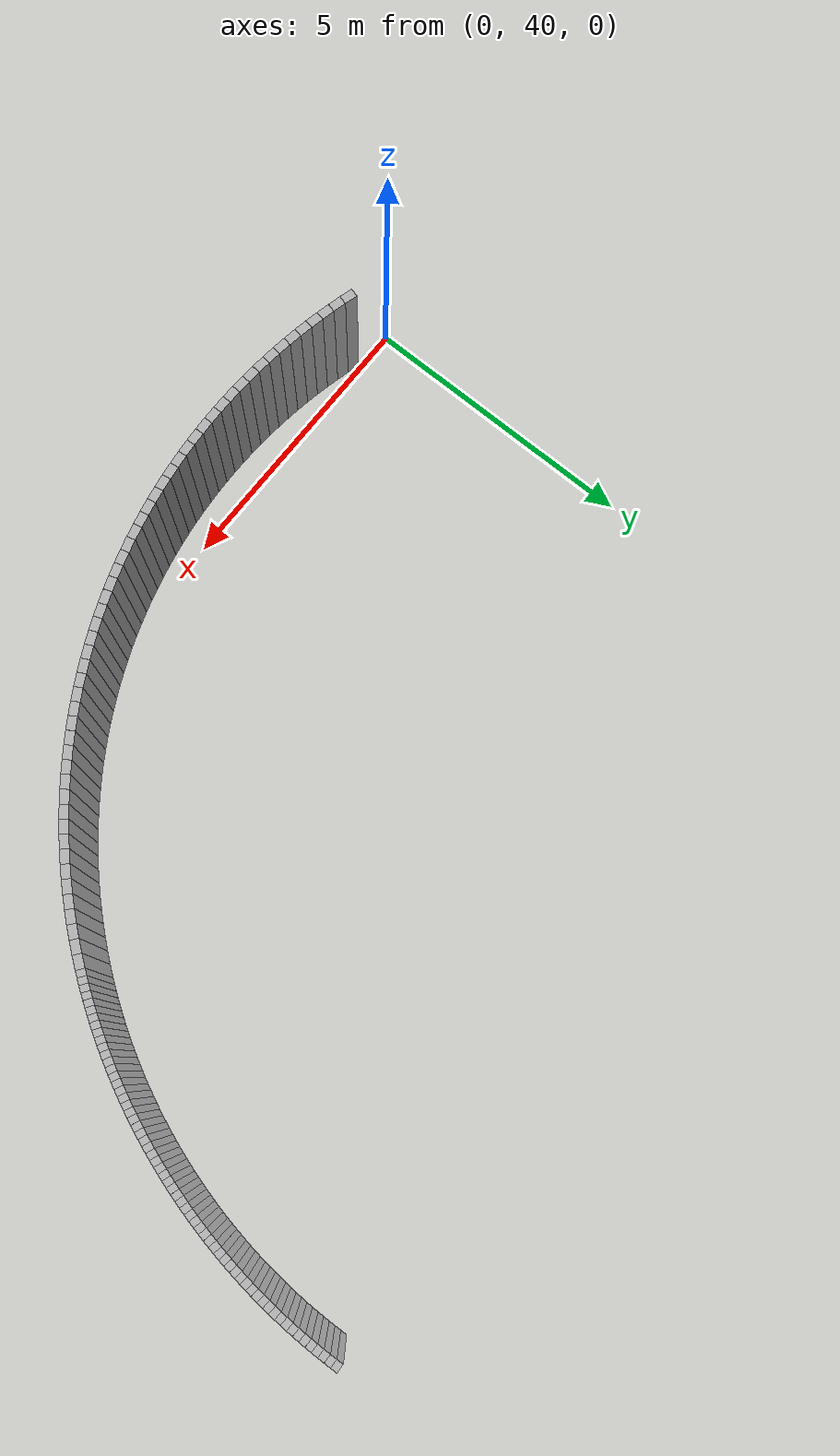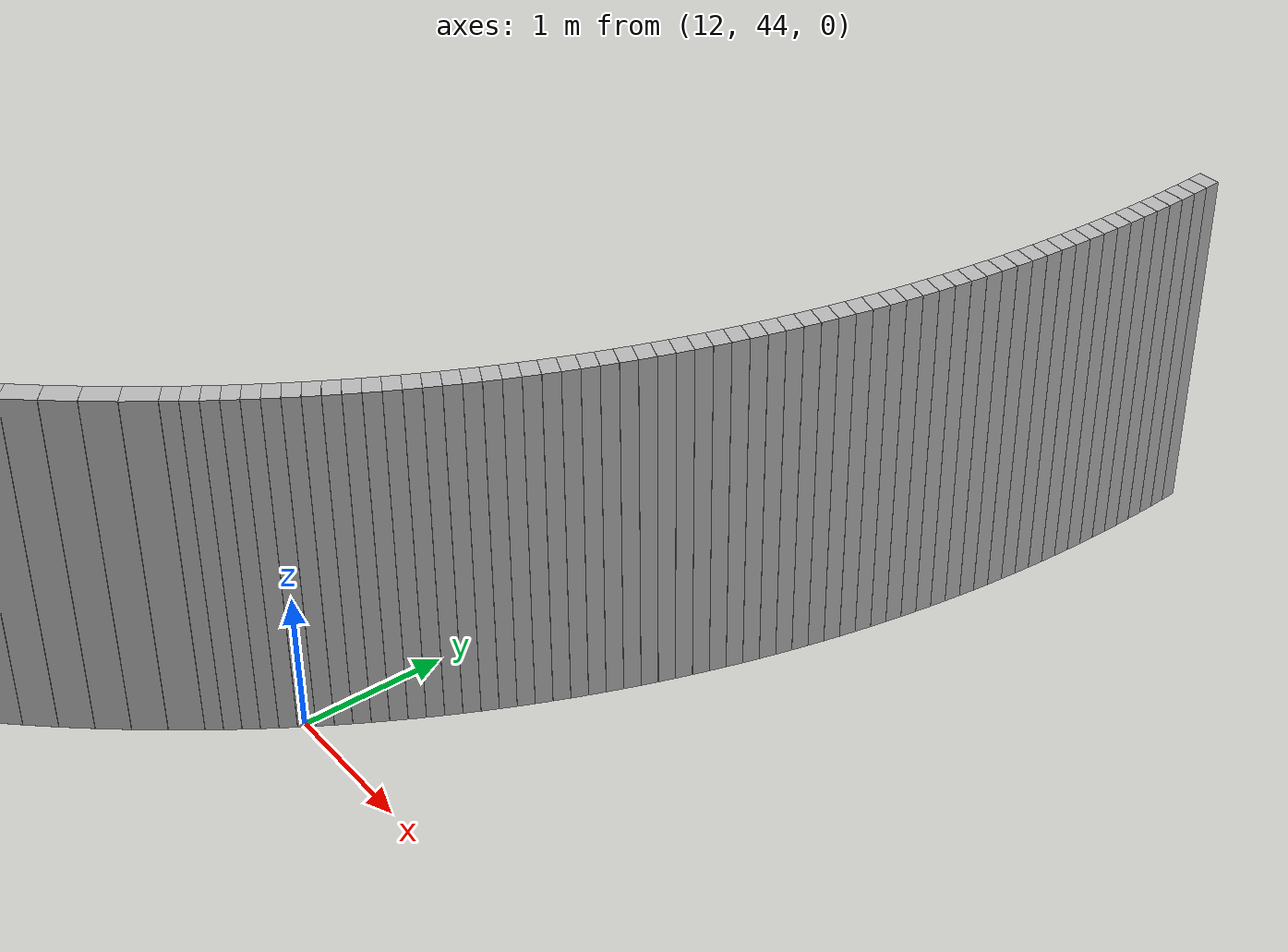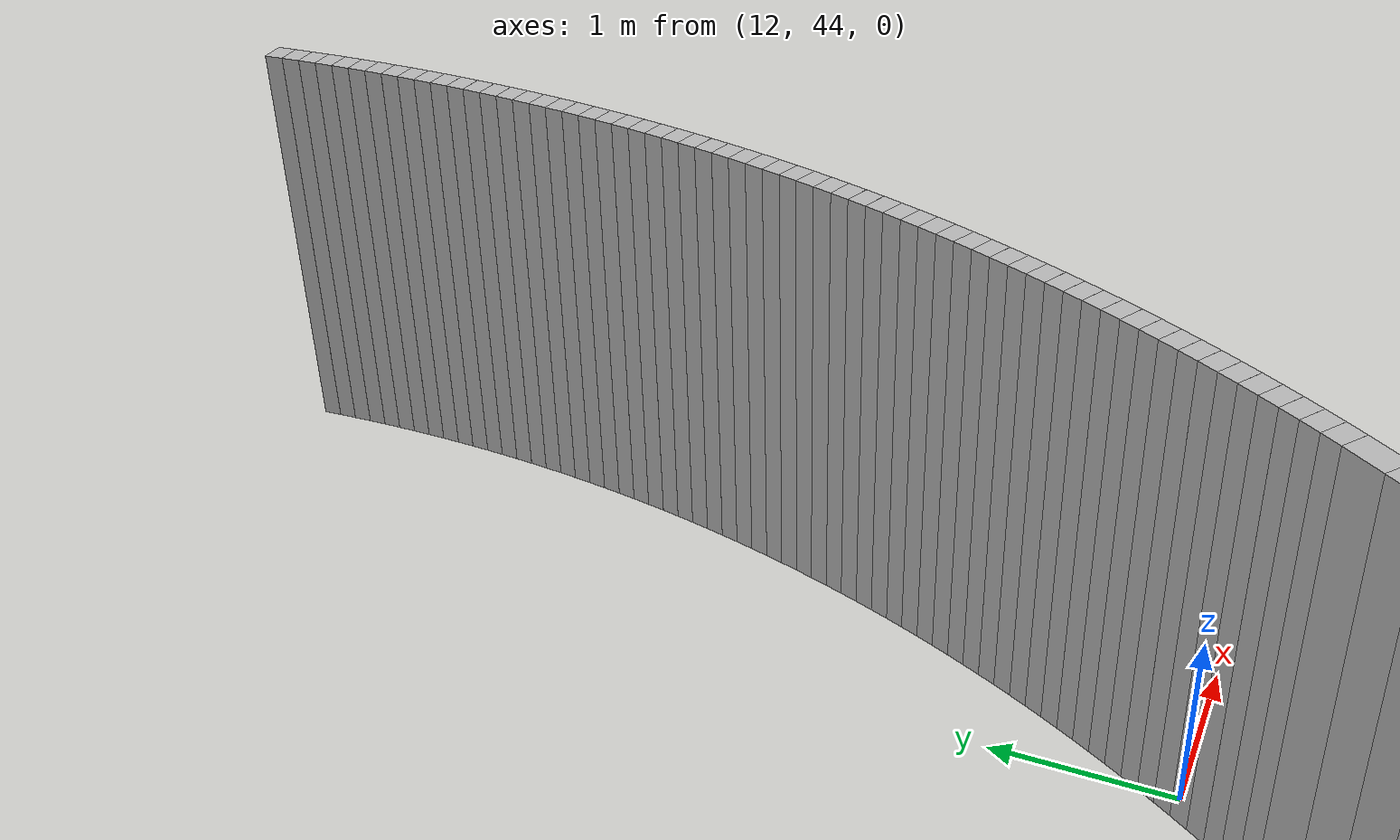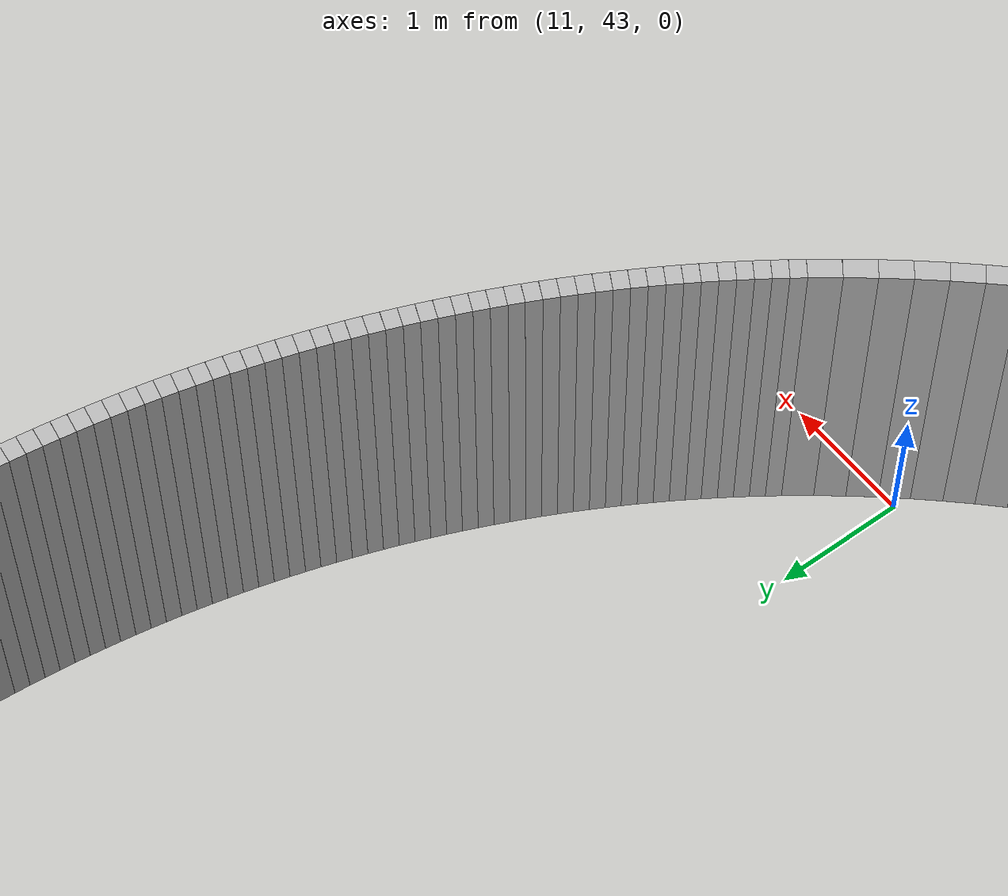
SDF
<?xml version="1.0" ?>
<sdf version="1.6">
  <model name="sps_4110">
    <pose frame="">0 0 0 0 -0 0</pose>
    <static>1</static>
    <self_collide>0</self_collide>
    <allow_auto_disable>0</allow_auto_disable>
    <link name="Wall7954">
      <kinematic>0</kinematic>
      <gravity>1</gravity>
      <self_collide>0</self_collide>
      <collision name="collision">
        <geometry>
          <box>
            <size>0.227303 0.15 2.5</size>
          </box>
        </geometry>
        <pose frame="">0 0 0 0 -0 0</pose>
      </collision>
      <visual name="visual">
        <geometry>
          <box>
            <size>0.227303 0.15 2.5</size>
          </box>
        </geometry>
        <pose frame="">0 0 0 0 -0 0</pose>
        <cast_shadows>1</cast_shadows>
        <transparency>0.0</transparency>
      </visual>
      <pose frame="">0.788841 39.8388 1.25 0 0 -0.281066</pose>
    </link>
    <link name="Wall7955">
      <kinematic>0</kinematic>
      <gravity>1</gravity>
      <self_collide>0</self_collide>
      <collision name="collision">
        <geometry>
          <box>
            <size>0.227543 0.15 2.5</size>
          </box>
        </geometry>
        <pose frame="">0 0 0 0 -0 0</pose>
      </collision>
      <visual name="visual">
        <geometry>
          <box>
            <size>0.227543 0.15 2.5</size>
          </box>
        </geometry>
        <pose frame="">0 0 0 0 -0 0</pose>
        <cast_shadows>1</cast_shadows>
        <transparency>0.0</transparency>
      </visual>
      <pose frame="">1.00805 39.7783 1.25 0 0 -0.257665</pose>
    </link>
    <link name="Wall7956">
      <kinematic>0</kinematic>
      <gravity>1</gravity>
      <self_collide>0</self_collide>
      <collision name="collision">
        <geometry>
          <box>
            <size>0.227405 0.15 2.5</size>
          </box>
        </geometry>
        <pose frame="">0 0 0 0 -0 0</pose>
      </collision>
      <visual name="visual">
        <geometry>
          <box>
            <size>0.227405 0.15 2.5</size>
          </box>
        </geometry>
        <pose frame="">0 0 0 0 -0 0</pose>
        <cast_shadows>1</cast_shadows>
        <transparency>0.0</transparency>
      </visual>
      <pose frame="">1.22866 39.7229 1.25 0 0 -0.234303</pose>
    </link>
    <link name="Wall7957">
      <kinematic>0</kinematic>
      <gravity>1</gravity>
      <self_collide>0</self_collide>
      <collision name="collision">
        <geometry>
          <box>
            <size>0.227527 0.15 2.5</size>
          </box>
        </geometry>
        <pose frame="">0 0 0 0 -0 0</pose>
      </collision>
      <visual name="visual">
        <geometry>
          <box>
            <size>0.227527 0.15 2.5</size>
          </box>
        </geometry>
        <pose frame="">0 0 0 0 -0 0</pose>
        <cast_shadows>1</cast_shadows>
        <transparency>0.0</transparency>
      </visual>
      <pose frame="">1.45046 39.6725 1.25 0 0 -0.212442</pose>
    </link>
    <link name="Wall7958">
      <kinematic>0</kinematic>
      <gravity>1</gravity>
      <self_collide>0</self_collide>
      <collision name="collision">
        <geometry>
          <box>
            <size>0.227281 0.15 2.5</size>
          </box>
        </geometry>
        <pose frame="">0 0 0 0 -0 0</pose>
      </collision>
      <visual name="visual">
        <geometry>
          <box>
            <size>0.227281 0.15 2.5</size>
          </box>
        </geometry>
        <pose frame="">0 0 0 0 -0 0</pose>
        <cast_shadows>1</cast_shadows>
        <transparency>0.0</transparency>
      </visual>
      <pose frame="">1.67327 39.6271 1.25 0 0 -0.189654</pose>
    </link>
    <link name="Wall7959">
      <kinematic>0</kinematic>
      <gravity>1</gravity>
      <self_collide>0</self_collide>
      <collision name="collision">
        <geometry>
          <box>
            <size>0.227494 0.15 2.5</size>
          </box>
        </geometry>
        <pose frame="">0 0 0 0 -0 0</pose>
      </collision>
      <visual name="visual">
        <geometry>
          <box>
            <size>0.227494 0.15 2.5</size>
          </box>
        </geometry>
        <pose frame="">0 0 0 0 -0 0</pose>
        <cast_shadows>1</cast_shadows>
        <transparency>0.0</transparency>
      </visual>
      <pose frame="">1.89706 39.5869 1.25 0 0 -0.166031</pose>
    </link>
    <link name="Wall7960">
      <kinematic>0</kinematic>
      <gravity>1</gravity>
      <self_collide>0</self_collide>
      <collision name="collision">
        <geometry>
          <box>
            <size>0.227385 0.15 2.5</size>
          </box>
        </geometry>
        <pose frame="">0 0 0 0 -0 0</pose>
      </collision>
      <visual name="visual">
        <geometry>
          <box>
            <size>0.227385 0.15 2.5</size>
          </box>
        </geometry>
        <pose frame="">0 0 0 0 -0 0</pose>
        <cast_shadows>1</cast_shadows>
        <transparency>0.0</transparency>
      </visual>
      <pose frame="">2.12176 39.5518 1.25 0 0 -0.143833</pose>
    </link>
    <link name="Wall7961">
      <kinematic>0</kinematic>
      <gravity>1</gravity>
      <self_collide>0</self_collide>
      <collision name="collision">
        <geometry>
          <box>
            <size>0.227448 0.15 2.5</size>
          </box>
        </geometry>
        <pose frame="">0 0 0 0 -0 0</pose>
      </collision>
      <visual name="visual">
        <geometry>
          <box>
            <size>0.227448 0.15 2.5</size>
          </box>
        </geometry>
        <pose frame="">0 0 0 0 -0 0</pose>
        <cast_shadows>1</cast_shadows>
        <transparency>0.0</transparency>
      </visual>
      <pose frame="">2.34716 39.5217 1.25 0 0 -0.121592</pose>
    </link>
    <link name="Wall7962">
      <kinematic>0</kinematic>
      <gravity>1</gravity>
      <self_collide>0</self_collide>
      <collision name="collision">
        <geometry>
          <box>
            <size>0.227528 0.15 2.5</size>
          </box>
        </geometry>
        <pose frame="">0 0 0 0 -0 0</pose>
      </collision>
      <visual name="visual">
        <geometry>
          <box>
            <size>0.227528 0.15 2.5</size>
          </box>
        </geometry>
        <pose frame="">0 0 0 0 -0 0</pose>
        <cast_shadows>1</cast_shadows>
        <transparency>0.0</transparency>
      </visual>
      <pose frame="">2.57326 39.4968 1.25 0 0 -0.0978002</pose>
    </link>
    <link name="Wall7963">
      <kinematic>0</kinematic>
      <gravity>1</gravity>
      <self_collide>0</self_collide>
      <collision name="collision">
        <geometry>
          <box>
            <size>0.227412 0.15 2.5</size>
          </box>
        </geometry>
        <pose frame="">0 0 0 0 -0 0</pose>
      </collision>
      <visual name="visual">
        <geometry>
          <box>
            <size>0.227412 0.15 2.5</size>
          </box>
        </geometry>
        <pose frame="">0 0 0 0 -0 0</pose>
        <cast_shadows>1</cast_shadows>
        <transparency>0.0</transparency>
      </visual>
      <pose frame="">2.79986 39.477 1.25 0 0 -0.076566</pose>
    </link>
    <link name="Wall7964">
      <kinematic>0</kinematic>
      <gravity>1</gravity>
      <self_collide>0</self_collide>
      <collision name="collision">
        <geometry>
          <box>
            <size>0.227549 0.15 2.5</size>
          </box>
        </geometry>
        <pose frame="">0 0 0 0 -0 0</pose>
      </collision>
      <visual name="visual">
        <geometry>
          <box>
            <size>0.227549 0.15 2.5</size>
          </box>
        </geometry>
        <pose frame="">0 0 0 0 -0 0</pose>
        <cast_shadows>1</cast_shadows>
        <transparency>0.0</transparency>
      </visual>
      <pose frame="">3.02685 39.4623 1.25 0 0 -0.0525972</pose>
    </link>
    <link name="Wall7965">
      <kinematic>0</kinematic>
      <gravity>1</gravity>
      <self_collide>0</self_collide>
      <collision name="collision">
        <geometry>
          <box>
            <size>0.227276 0.15 2.5</size>
          </box>
        </geometry>
        <pose frame="">0 0 0 0 -0 0</pose>
      </collision>
      <visual name="visual">
        <geometry>
          <box>
            <size>0.227276 0.15 2.5</size>
          </box>
        </geometry>
        <pose frame="">0 0 0 0 -0 0</pose>
        <cast_shadows>1</cast_shadows>
        <transparency>0.0</transparency>
      </visual>
      <pose frame="">3.25405 39.4529 1.25 0 0 -0.0300823</pose>
    </link>
    <link name="Wall7966">
      <kinematic>0</kinematic>
      <gravity>1</gravity>
      <self_collide>0</self_collide>
      <collision name="collision">
        <geometry>
          <box>
            <size>0.227607 0.15 2.5</size>
          </box>
        </geometry>
        <pose frame="">0 0 0 0 -0 0</pose>
      </collision>
      <visual name="visual">
        <geometry>
          <box>
            <size>0.227607 0.15 2.5</size>
          </box>
        </geometry>
        <pose frame="">0 0 0 0 -0 0</pose>
        <cast_shadows>1</cast_shadows>
        <transparency>0.0</transparency>
      </visual>
      <pose frame="">3.48144 39.4486 1.25 0 0 -0.00777672</pose>
    </link>
    <link name="Wall7967">
      <kinematic>0</kinematic>
      <gravity>1</gravity>
      <self_collide>0</self_collide>
      <collision name="collision">
        <geometry>
          <box>
            <size>0.227442 0.15 2.5</size>
          </box>
        </geometry>
        <pose frame="">0 0 0 0 -0 0</pose>
      </collision>
      <visual name="visual">
        <geometry>
          <box>
            <size>0.227442 0.15 2.5</size>
          </box>
        </geometry>
        <pose frame="">0 0 0 0 -0 0</pose>
        <cast_shadows>1</cast_shadows>
        <transparency>0.0</transparency>
      </visual>
      <pose frame="">3.70895 39.4494 1.25 0 -0 0.0147601</pose>
    </link>
    <link name="Wall7968">
      <kinematic>0</kinematic>
      <gravity>1</gravity>
      <self_collide>0</self_collide>
      <collision name="collision">
        <geometry>
          <box>
            <size>0.227345 0.15 2.5</size>
          </box>
        </geometry>
        <pose frame="">0 0 0 0 -0 0</pose>
      </collision>
      <visual name="visual">
        <geometry>
          <box>
            <size>0.227345 0.15 2.5</size>
          </box>
        </geometry>
        <pose frame="">0 0 0 0 -0 0</pose>
        <cast_shadows>1</cast_shadows>
        <transparency>0.0</transparency>
      </visual>
      <pose frame="">3.93624 39.4555 1.25 0 -0 0.0389379</pose>
    </link>
    <link name="Wall7969">
      <kinematic>0</kinematic>
      <gravity>1</gravity>
      <self_collide>0</self_collide>
      <collision name="collision">
        <geometry>
          <box>
            <size>0.227638 0.15 2.5</size>
          </box>
        </geometry>
        <pose frame="">0 0 0 0 -0 0</pose>
      </collision>
      <visual name="visual">
        <geometry>
          <box>
            <size>0.227638 0.15 2.5</size>
          </box>
        </geometry>
        <pose frame="">0 0 0 0 -0 0</pose>
        <cast_shadows>1</cast_shadows>
        <transparency>0.0</transparency>
      </visual>
      <pose frame="">4.16344 39.4667 1.25 0 -0 0.0595588</pose>
    </link>
    <link name="Wall7970">
      <kinematic>0</kinematic>
      <gravity>1</gravity>
      <self_collide>0</self_collide>
      <collision name="collision">
        <geometry>
          <box>
            <size>0.227422 0.15 2.5</size>
          </box>
        </geometry>
        <pose frame="">0 0 0 0 -0 0</pose>
      </collision>
      <visual name="visual">
        <geometry>
          <box>
            <size>0.227422 0.15 2.5</size>
          </box>
        </geometry>
        <pose frame="">0 0 0 0 -0 0</pose>
        <cast_shadows>1</cast_shadows>
        <transparency>0.0</transparency>
      </visual>
      <pose frame="">4.39037 39.483 1.25 0 -0 0.0838321</pose>
    </link>
    <link name="Wall7971">
      <kinematic>0</kinematic>
      <gravity>1</gravity>
      <self_collide>0</self_collide>
      <collision name="collision">
        <geometry>
          <box>
            <size>0.227484 0.15 2.5</size>
          </box>
        </geometry>
        <pose frame="">0 0 0 0 -0 0</pose>
      </collision>
      <visual name="visual">
        <geometry>
          <box>
            <size>0.227484 0.15 2.5</size>
          </box>
        </geometry>
        <pose frame="">0 0 0 0 -0 0</pose>
        <cast_shadows>1</cast_shadows>
        <transparency>0.0</transparency>
      </visual>
      <pose frame="">4.61678 39.5046 1.25 0 -0 0.10645</pose>
    </link>
    <link name="Wall7972">
      <kinematic>0</kinematic>
      <gravity>1</gravity>
      <self_collide>0</self_collide>
      <collision name="collision">
        <geometry>
          <box>
            <size>0.227473 0.15 2.5</size>
          </box>
        </geometry>
        <pose frame="">0 0 0 0 -0 0</pose>
      </collision>
      <visual name="visual">
        <geometry>
          <box>
            <size>0.227473 0.15 2.5</size>
          </box>
        </geometry>
        <pose frame="">0 0 0 0 -0 0</pose>
        <cast_shadows>1</cast_shadows>
        <transparency>0.0</transparency>
      </visual>
      <pose frame="">4.84267 39.5313 1.25 0 -0 0.128881</pose>
    </link>
    <link name="Wall7973">
      <kinematic>0</kinematic>
      <gravity>1</gravity>
      <self_collide>0</self_collide>
      <collision name="collision">
        <geometry>
          <box>
            <size>0.227404 0.15 2.5</size>
          </box>
        </geometry>
        <pose frame="">0 0 0 0 -0 0</pose>
      </collision>
      <visual name="visual">
        <geometry>
          <box>
            <size>0.227404 0.15 2.5</size>
          </box>
        </geometry>
        <pose frame="">0 0 0 0 -0 0</pose>
        <cast_shadows>1</cast_shadows>
        <transparency>0.0</transparency>
      </visual>
      <pose frame="">5.06786 39.5631 1.25 0 -0 0.15169</pose>
    </link>
    <link name="Wall7974">
      <kinematic>0</kinematic>
      <gravity>1</gravity>
      <self_collide>0</self_collide>
      <collision name="collision">
        <geometry>
          <box>
            <size>0.227443 0.15 2.5</size>
          </box>
        </geometry>
        <pose frame="">0 0 0 0 -0 0</pose>
      </collision>
      <visual name="visual">
        <geometry>
          <box>
            <size>0.227443 0.15 2.5</size>
          </box>
        </geometry>
        <pose frame="">0 0 0 0 -0 0</pose>
        <cast_shadows>1</cast_shadows>
        <transparency>0.0</transparency>
      </visual>
      <pose frame="">5.29226 39.6 1.25 0 -0 0.174237</pose>
    </link>
    <link name="Wall7975">
      <kinematic>0</kinematic>
      <gravity>1</gravity>
      <self_collide>0</self_collide>
      <collision name="collision">
        <geometry>
          <box>
            <size>0.227442 0.15 2.5</size>
          </box>
        </geometry>
        <pose frame="">0 0 0 0 -0 0</pose>
      </collision>
      <visual name="visual">
        <geometry>
          <box>
            <size>0.227442 0.15 2.5</size>
          </box>
        </geometry>
        <pose frame="">0 0 0 0 -0 0</pose>
        <cast_shadows>1</cast_shadows>
        <transparency>0.0</transparency>
      </visual>
      <pose frame="">5.51577 39.642 1.25 0 -0 0.197448</pose>
    </link>
    <link name="Wall7976">
      <kinematic>0</kinematic>
      <gravity>1</gravity>
      <self_collide>0</self_collide>
      <collision name="collision">
        <geometry>
          <box>
            <size>0.22745 0.15 2.5</size>
          </box>
        </geometry>
        <pose frame="">0 0 0 0 -0 0</pose>
      </collision>
      <visual name="visual">
        <geometry>
          <box>
            <size>0.22745 0.15 2.5</size>
          </box>
        </geometry>
        <pose frame="">0 0 0 0 -0 0</pose>
        <cast_shadows>1</cast_shadows>
        <transparency>0.0</transparency>
      </visual>
      <pose frame="">5.73827 39.6891 1.25 0 -0 0.219659</pose>
    </link>
    <link name="Wall7977">
      <kinematic>0</kinematic>
      <gravity>1</gravity>
      <self_collide>0</self_collide>
      <collision name="collision">
        <geometry>
          <box>
            <size>0.227422 0.15 2.5</size>
          </box>
        </geometry>
        <pose frame="">0 0 0 0 -0 0</pose>
      </collision>
      <visual name="visual">
        <geometry>
          <box>
            <size>0.227422 0.15 2.5</size>
          </box>
        </geometry>
        <pose frame="">0 0 0 0 -0 0</pose>
        <cast_shadows>1</cast_shadows>
        <transparency>0.0</transparency>
      </visual>
      <pose frame="">5.95965 39.7412 1.25 0 -0 0.24257</pose>
    </link>
    <link name="Wall7978">
      <kinematic>0</kinematic>
      <gravity>1</gravity>
      <self_collide>0</self_collide>
      <collision name="collision">
        <geometry>
          <box>
            <size>0.227364 0.15 2.5</size>
          </box>
        </geometry>
        <pose frame="">0 0 0 0 -0 0</pose>
      </collision>
      <visual name="visual">
        <geometry>
          <box>
            <size>0.227364 0.15 2.5</size>
          </box>
        </geometry>
        <pose frame="">0 0 0 0 -0 0</pose>
        <cast_shadows>1</cast_shadows>
        <transparency>0.0</transparency>
      </visual>
      <pose frame="">6.17974 39.7983 1.25 0 -0 0.265098</pose>
    </link>
    <link name="Wall7979">
      <kinematic>0</kinematic>
      <gravity>1</gravity>
      <self_collide>0</self_collide>
      <collision name="collision">
        <geometry>
          <box>
            <size>0.227573 0.15 2.5</size>
          </box>
        </geometry>
        <pose frame="">0 0 0 0 -0 0</pose>
      </collision>
      <visual name="visual">
        <geometry>
          <box>
            <size>0.227573 0.15 2.5</size>
          </box>
        </geometry>
        <pose frame="">0 0 0 0 -0 0</pose>
        <cast_shadows>1</cast_shadows>
        <transparency>0.0</transparency>
      </visual>
      <pose frame="">6.39855 39.8604 1.25 0 -0 0.287989</pose>
    </link>
    <link name="Wall7980">
      <kinematic>0</kinematic>
      <gravity>1</gravity>
      <self_collide>0</self_collide>
      <collision name="collision">
        <geometry>
          <box>
            <size>0.22734 0.15 2.5</size>
          </box>
        </geometry>
        <pose frame="">0 0 0 0 -0 0</pose>
      </collision>
      <visual name="visual">
        <geometry>
          <box>
            <size>0.22734 0.15 2.5</size>
          </box>
        </geometry>
        <pose frame="">0 0 0 0 -0 0</pose>
        <cast_shadows>1</cast_shadows>
        <transparency>0.0</transparency>
      </visual>
      <pose frame="">6.61587 39.9275 1.25 0 -0 0.311053</pose>
    </link>
    <link name="Wall7981">
      <kinematic>0</kinematic>
      <gravity>1</gravity>
      <self_collide>0</self_collide>
      <collision name="collision">
        <geometry>
          <box>
            <size>0.227537 0.15 2.5</size>
          </box>
        </geometry>
        <pose frame="">0 0 0 0 -0 0</pose>
      </collision>
      <visual name="visual">
        <geometry>
          <box>
            <size>0.227537 0.15 2.5</size>
          </box>
        </geometry>
        <pose frame="">0 0 0 0 -0 0</pose>
        <cast_shadows>1</cast_shadows>
        <transparency>0.0</transparency>
      </visual>
      <pose frame="">6.83157 39.9996 1.25 0 -0 0.333966</pose>
    </link>
    <link name="Wall7982">
      <kinematic>0</kinematic>
      <gravity>1</gravity>
      <self_collide>0</self_collide>
      <collision name="collision">
        <geometry>
          <box>
            <size>0.22744 0.15 2.5</size>
          </box>
        </geometry>
        <pose frame="">0 0 0 0 -0 0</pose>
      </collision>
      <visual name="visual">
        <geometry>
          <box>
            <size>0.22744 0.15 2.5</size>
          </box>
        </geometry>
        <pose frame="">0 0 0 0 -0 0</pose>
        <cast_shadows>1</cast_shadows>
        <transparency>0.0</transparency>
      </visual>
      <pose frame="">7.04565 40.0765 1.25 0 -0 0.355787</pose>
    </link>
    <link name="Wall7983">
      <kinematic>0</kinematic>
      <gravity>1</gravity>
      <self_collide>0</self_collide>
      <collision name="collision">
        <geometry>
          <box>
            <size>0.227336 0.15 2.5</size>
          </box>
        </geometry>
        <pose frame="">0 0 0 0 -0 0</pose>
      </collision>
      <visual name="visual">
        <geometry>
          <box>
            <size>0.227336 0.15 2.5</size>
          </box>
        </geometry>
        <pose frame="">0 0 0 0 -0 0</pose>
        <cast_shadows>1</cast_shadows>
        <transparency>0.0</transparency>
      </visual>
      <pose frame="">7.25783 40.1582 1.25 0 -0 0.37926</pose>
    </link>
    <link name="Wall7984">
      <kinematic>0</kinematic>
      <gravity>1</gravity>
      <self_collide>0</self_collide>
      <collision name="collision">
        <geometry>
          <box>
            <size>0.227559 0.15 2.5</size>
          </box>
        </geometry>
        <pose frame="">0 0 0 0 -0 0</pose>
      </collision>
      <visual name="visual">
        <geometry>
          <box>
            <size>0.227559 0.15 2.5</size>
          </box>
        </geometry>
        <pose frame="">0 0 0 0 -0 0</pose>
        <cast_shadows>1</cast_shadows>
        <transparency>0.0</transparency>
      </visual>
      <pose frame="">7.46813 40.2448 1.25 0 -0 0.402074</pose>
    </link>
    <link name="Wall7985">
      <kinematic>0</kinematic>
      <gravity>1</gravity>
      <self_collide>0</self_collide>
      <collision name="collision">
        <geometry>
          <box>
            <size>0.22736 0.15 2.5</size>
          </box>
        </geometry>
        <pose frame="">0 0 0 0 -0 0</pose>
      </collision>
      <visual name="visual">
        <geometry>
          <box>
            <size>0.22736 0.15 2.5</size>
          </box>
        </geometry>
        <pose frame="">0 0 0 0 -0 0</pose>
        <cast_shadows>1</cast_shadows>
        <transparency>0.0</transparency>
      </visual>
      <pose frame="">7.67644 40.3361 1.25 0 -0 0.424139</pose>
    </link>
    <link name="Wall7986">
      <kinematic>0</kinematic>
      <gravity>1</gravity>
      <self_collide>0</self_collide>
      <collision name="collision">
        <geometry>
          <box>
            <size>0.227569 0.15 2.5</size>
          </box>
        </geometry>
        <pose frame="">0 0 0 0 -0 0</pose>
      </collision>
      <visual name="visual">
        <geometry>
          <box>
            <size>0.227569 0.15 2.5</size>
          </box>
        </geometry>
        <pose frame="">0 0 0 0 -0 0</pose>
        <cast_shadows>1</cast_shadows>
        <transparency>0.0</transparency>
      </visual>
      <pose frame="">7.88265 40.4321 1.25 0 -0 0.447094</pose>
    </link>
    <link name="Wall7987">
      <kinematic>0</kinematic>
      <gravity>1</gravity>
      <self_collide>0</self_collide>
      <collision name="collision">
        <geometry>
          <box>
            <size>0.227487 0.15 2.5</size>
          </box>
        </geometry>
        <pose frame="">0 0 0 0 -0 0</pose>
      </collision>
      <visual name="visual">
        <geometry>
          <box>
            <size>0.227487 0.15 2.5</size>
          </box>
        </geometry>
        <pose frame="">0 0 0 0 -0 0</pose>
        <cast_shadows>1</cast_shadows>
        <transparency>0.0</transparency>
      </visual>
      <pose frame="">8.08666 40.5328 1.25 0 -0 0.470007</pose>
    </link>
    <link name="Wall7988">
      <kinematic>0</kinematic>
      <gravity>1</gravity>
      <self_collide>0</self_collide>
      <collision name="collision">
        <geometry>
          <box>
            <size>0.227328 0.15 2.5</size>
          </box>
        </geometry>
        <pose frame="">0 0 0 0 -0 0</pose>
      </collision>
      <visual name="visual">
        <geometry>
          <box>
            <size>0.227328 0.15 2.5</size>
          </box>
        </geometry>
        <pose frame="">0 0 0 0 -0 0</pose>
        <cast_shadows>1</cast_shadows>
        <transparency>0.0</transparency>
      </visual>
      <pose frame="">8.28826 40.638 1.25 0 -0 0.491868</pose>
    </link>
    <link name="Wall7989">
      <kinematic>0</kinematic>
      <gravity>1</gravity>
      <self_collide>0</self_collide>
      <collision name="collision">
        <geometry>
          <box>
            <size>0.2276 0.15 2.5</size>
          </box>
        </geometry>
        <pose frame="">0 0 0 0 -0 0</pose>
      </collision>
      <visual name="visual">
        <geometry>
          <box>
            <size>0.2276 0.15 2.5</size>
          </box>
        </geometry>
        <pose frame="">0 0 0 0 -0 0</pose>
        <cast_shadows>1</cast_shadows>
        <transparency>0.0</transparency>
      </visual>
      <pose frame="">8.48745 40.7478 1.25 0 -0 0.51572</pose>
    </link>
    <link name="Wall7990">
      <kinematic>0</kinematic>
      <gravity>1</gravity>
      <self_collide>0</self_collide>
      <collision name="collision">
        <geometry>
          <box>
            <size>0.227353 0.15 2.5</size>
          </box>
        </geometry>
        <pose frame="">0 0 0 0 -0 0</pose>
      </collision>
      <visual name="visual">
        <geometry>
          <box>
            <size>0.227353 0.15 2.5</size>
          </box>
        </geometry>
        <pose frame="">0 0 0 0 -0 0</pose>
        <cast_shadows>1</cast_shadows>
        <transparency>0.0</transparency>
      </visual>
      <pose frame="">8.68404 40.8622 1.25 0 -0 0.538394</pose>
    </link>
    <link name="Wall7991">
      <kinematic>0</kinematic>
      <gravity>1</gravity>
      <self_collide>0</self_collide>
      <collision name="collision">
        <geometry>
          <box>
            <size>0.227495 0.15 2.5</size>
          </box>
        </geometry>
        <pose frame="">0 0 0 0 -0 0</pose>
      </collision>
      <visual name="visual">
        <geometry>
          <box>
            <size>0.227495 0.15 2.5</size>
          </box>
        </geometry>
        <pose frame="">0 0 0 0 -0 0</pose>
        <cast_shadows>1</cast_shadows>
        <transparency>0.0</transparency>
      </visual>
      <pose frame="">8.87795 40.981 1.25 0 -0 0.560988</pose>
    </link>
    <link name="Wall7992">
      <kinematic>0</kinematic>
      <gravity>1</gravity>
      <self_collide>0</self_collide>
      <collision name="collision">
        <geometry>
          <box>
            <size>0.227482 0.15 2.5</size>
          </box>
        </geometry>
        <pose frame="">0 0 0 0 -0 0</pose>
      </collision>
      <visual name="visual">
        <geometry>
          <box>
            <size>0.227482 0.15 2.5</size>
          </box>
        </geometry>
        <pose frame="">0 0 0 0 -0 0</pose>
        <cast_shadows>1</cast_shadows>
        <transparency>0.0</transparency>
      </visual>
      <pose frame="">9.06918 41.1042 1.25 0 -0 0.583687</pose>
    </link>
    <link name="Wall7993">
      <kinematic>0</kinematic>
      <gravity>1</gravity>
      <self_collide>0</self_collide>
      <collision name="collision">
        <geometry>
          <box>
            <size>0.227351 0.15 2.5</size>
          </box>
        </geometry>
        <pose frame="">0 0 0 0 -0 0</pose>
      </collision>
      <visual name="visual">
        <geometry>
          <box>
            <size>0.227351 0.15 2.5</size>
          </box>
        </geometry>
        <pose frame="">0 0 0 0 -0 0</pose>
        <cast_shadows>1</cast_shadows>
        <transparency>0.0</transparency>
      </visual>
      <pose frame="">9.25747 41.2317 1.25 0 -0 0.606767</pose>
    </link>
    <link name="Wall7994">
      <kinematic>0</kinematic>
      <gravity>1</gravity>
      <self_collide>0</self_collide>
      <collision name="collision">
        <geometry>
          <box>
            <size>0.227515 0.15 2.5</size>
          </box>
        </geometry>
        <pose frame="">0 0 0 0 -0 0</pose>
      </collision>
      <visual name="visual">
        <geometry>
          <box>
            <size>0.227515 0.15 2.5</size>
          </box>
        </geometry>
        <pose frame="">0 0 0 0 -0 0</pose>
        <cast_shadows>1</cast_shadows>
        <transparency>0.0</transparency>
      </visual>
      <pose frame="">9.44286 41.3634 1.25 0 -0 0.628638</pose>
    </link>
    <link name="Wall7995">
      <kinematic>0</kinematic>
      <gravity>1</gravity>
      <self_collide>0</self_collide>
      <collision name="collision">
        <geometry>
          <box>
            <size>0.227437 0.15 2.5</size>
          </box>
        </geometry>
        <pose frame="">0 0 0 0 -0 0</pose>
      </collision>
      <visual name="visual">
        <geometry>
          <box>
            <size>0.227437 0.15 2.5</size>
          </box>
        </geometry>
        <pose frame="">0 0 0 0 -0 0</pose>
        <cast_shadows>1</cast_shadows>
        <transparency>0.0</transparency>
      </visual>
      <pose frame="">9.62527 41.4993 1.25 0 -0 0.651981</pose>
    </link>
    <link name="Wall7996">
      <kinematic>0</kinematic>
      <gravity>1</gravity>
      <self_collide>0</self_collide>
      <collision name="collision">
        <geometry>
          <box>
            <size>0.227378 0.15 2.5</size>
          </box>
        </geometry>
        <pose frame="">0 0 0 0 -0 0</pose>
      </collision>
      <visual name="visual">
        <geometry>
          <box>
            <size>0.227378 0.15 2.5</size>
          </box>
        </geometry>
        <pose frame="">0 0 0 0 -0 0</pose>
        <cast_shadows>1</cast_shadows>
        <transparency>0.0</transparency>
      </visual>
      <pose frame="">9.80447 41.6393 1.25 0 -0 0.674322</pose>
    </link>
    <link name="Wall7997">
      <kinematic>0</kinematic>
      <gravity>1</gravity>
      <self_collide>0</self_collide>
      <collision name="collision">
        <geometry>
          <box>
            <size>0.227582 0.15 2.5</size>
          </box>
        </geometry>
        <pose frame="">0 0 0 0 -0 0</pose>
      </collision>
      <visual name="visual">
        <geometry>
          <box>
            <size>0.227582 0.15 2.5</size>
          </box>
        </geometry>
        <pose frame="">0 0 0 0 -0 0</pose>
        <cast_shadows>1</cast_shadows>
        <transparency>0.0</transparency>
      </visual>
      <pose frame="">9.98046 41.7834 1.25 0 -0 0.697863</pose>
    </link>
    <link name="Wall7998">
      <kinematic>0</kinematic>
      <gravity>1</gravity>
      <self_collide>0</self_collide>
      <collision name="collision">
        <geometry>
          <box>
            <size>0.227458 0.15 2.5</size>
          </box>
        </geometry>
        <pose frame="">0 0 0 0 -0 0</pose>
      </collision>
      <visual name="visual">
        <geometry>
          <box>
            <size>0.227458 0.15 2.5</size>
          </box>
        </geometry>
        <pose frame="">0 0 0 0 -0 0</pose>
        <cast_shadows>1</cast_shadows>
        <transparency>0.0</transparency>
      </visual>
      <pose frame="">10.1532 41.9315 1.25 0 -0 0.71989</pose>
    </link>
    <link name="Wall7999">
      <kinematic>0</kinematic>
      <gravity>1</gravity>
      <self_collide>0</self_collide>
      <collision name="collision">
        <geometry>
          <box>
            <size>0.227481 0.15 2.5</size>
          </box>
        </geometry>
        <pose frame="">0 0 0 0 -0 0</pose>
      </collision>
      <visual name="visual">
        <geometry>
          <box>
            <size>0.227481 0.15 2.5</size>
          </box>
        </geometry>
        <pose frame="">0 0 0 0 -0 0</pose>
        <cast_shadows>1</cast_shadows>
        <transparency>0.0</transparency>
      </visual>
      <pose frame="">10.3225 42.0834 1.25 0 -0 0.742508</pose>
    </link>
    <link name="Wall8000">
      <kinematic>0</kinematic>
      <gravity>1</gravity>
      <self_collide>0</self_collide>
      <collision name="collision">
        <geometry>
          <box>
            <size>0.227447 0.15 2.5</size>
          </box>
        </geometry>
        <pose frame="">0 0 0 0 -0 0</pose>
      </collision>
      <visual name="visual">
        <geometry>
          <box>
            <size>0.227447 0.15 2.5</size>
          </box>
        </geometry>
        <pose frame="">0 0 0 0 -0 0</pose>
        <cast_shadows>1</cast_shadows>
        <transparency>0.0</transparency>
      </visual>
      <pose frame="">10.4883 42.2391 1.25 0 -0 0.765473</pose>
    </link>
    <link name="Wall8001">
      <kinematic>0</kinematic>
      <gravity>1</gravity>
      <self_collide>0</self_collide>
      <collision name="collision">
        <geometry>
          <box>
            <size>0.227402 0.15 2.5</size>
          </box>
        </geometry>
        <pose frame="">0 0 0 0 -0 0</pose>
      </collision>
      <visual name="visual">
        <geometry>
          <box>
            <size>0.227402 0.15 2.5</size>
          </box>
        </geometry>
        <pose frame="">0 0 0 0 -0 0</pose>
        <cast_shadows>1</cast_shadows>
        <transparency>0.0</transparency>
      </visual>
      <pose frame="">10.6505 42.3985 1.25 0 -0 0.787865</pose>
    </link>
    <link name="Wall8002">
      <kinematic>0</kinematic>
      <gravity>1</gravity>
      <self_collide>0</self_collide>
      <collision name="collision">
        <geometry>
          <box>
            <size>0.227481 0.15 2.5</size>
          </box>
        </geometry>
        <pose frame="">0 0 0 0 -0 0</pose>
      </collision>
      <visual name="visual">
        <geometry>
          <box>
            <size>0.227481 0.15 2.5</size>
          </box>
        </geometry>
        <pose frame="">0 0 0 0 -0 0</pose>
        <cast_shadows>1</cast_shadows>
        <transparency>0.0</transparency>
      </visual>
      <pose frame="">10.809 42.5616 1.25 0 -0 0.811773</pose>
    </link>
    <link name="Wall8003">
      <kinematic>0</kinematic>
      <gravity>1</gravity>
      <self_collide>0</self_collide>
      <collision name="collision">
        <geometry>
          <box>
            <size>0.227409 0.15 2.5</size>
          </box>
        </geometry>
        <pose frame="">0 0 0 0 -0 0</pose>
      </collision>
      <visual name="visual">
        <geometry>
          <box>
            <size>0.227409 0.15 2.5</size>
          </box>
        </geometry>
        <pose frame="">0 0 0 0 -0 0</pose>
        <cast_shadows>1</cast_shadows>
        <transparency>0.0</transparency>
      </visual>
      <pose frame="">10.9636 42.7283 1.25 0 -0 0.833812</pose>
    </link>
    <link name="Wall8004">
      <kinematic>0</kinematic>
      <gravity>1</gravity>
      <self_collide>0</self_collide>
      <collision name="collision">
        <geometry>
          <box>
            <size>0.227368 0.15 2.5</size>
          </box>
        </geometry>
        <pose frame="">0 0 0 0 -0 0</pose>
      </collision>
      <visual name="visual">
        <geometry>
          <box>
            <size>0.227368 0.15 2.5</size>
          </box>
        </geometry>
        <pose frame="">0 0 0 0 -0 0</pose>
        <cast_shadows>1</cast_shadows>
        <transparency>0.0</transparency>
      </visual>
      <pose frame="">11.1146 42.8984 1.25 0 -0 0.856259</pose>
    </link>
    <link name="Wall8005">
      <kinematic>0</kinematic>
      <gravity>1</gravity>
      <self_collide>0</self_collide>
      <collision name="collision">
        <geometry>
          <box>
            <size>0.227457 0.15 2.5</size>
          </box>
        </geometry>
        <pose frame="">0 0 0 0 -0 0</pose>
      </collision>
      <visual name="visual">
        <geometry>
          <box>
            <size>0.227457 0.15 2.5</size>
          </box>
        </geometry>
        <pose frame="">0 0 0 0 -0 0</pose>
        <cast_shadows>1</cast_shadows>
        <transparency>0.0</transparency>
      </visual>
      <pose frame="">11.2616 43.0719 1.25 0 -0 0.879459</pose>
    </link>
    <link name="Wall8006">
      <kinematic>0</kinematic>
      <gravity>1</gravity>
      <self_collide>0</self_collide>
      <collision name="collision">
        <geometry>
          <box>
            <size>0.227506 0.15 2.5</size>
          </box>
        </geometry>
        <pose frame="">0 0 0 0 -0 0</pose>
      </collision>
      <visual name="visual">
        <geometry>
          <box>
            <size>0.227506 0.15 2.5</size>
          </box>
        </geometry>
        <pose frame="">0 0 0 0 -0 0</pose>
        <cast_shadows>1</cast_shadows>
        <transparency>0.0</transparency>
      </visual>
      <pose frame="">11.4047 43.2487 1.25 0 -0 0.901376</pose>
    </link>
    <link name="Wall8007">
      <kinematic>0</kinematic>
      <gravity>1</gravity>
      <self_collide>0</self_collide>
      <collision name="collision">
        <geometry>
          <box>
            <size>0.227369 0.15 2.5</size>
          </box>
        </geometry>
        <pose frame="">0 0 0 0 -0 0</pose>
      </collision>
      <visual name="visual">
        <geometry>
          <box>
            <size>0.227369 0.15 2.5</size>
          </box>
        </geometry>
        <pose frame="">0 0 0 0 -0 0</pose>
        <cast_shadows>1</cast_shadows>
        <transparency>0.0</transparency>
      </visual>
      <pose frame="">11.5437 43.4287 1.25 0 -0 0.924987</pose>
    </link>
    <link name="Wall8008">
      <kinematic>0</kinematic>
      <gravity>1</gravity>
      <self_collide>0</self_collide>
      <collision name="collision">
        <geometry>
          <box>
            <size>0.113621 0.15 2.5</size>
          </box>
        </geometry>
        <pose frame="">0 0 0 0 -0 0</pose>
      </collision>
      <visual name="visual">
        <geometry>
          <box>
            <size>0.113621 0.15 2.5</size>
          </box>
        </geometry>
        <pose frame="">0 0 0 0 -0 0</pose>
        <cast_shadows>1</cast_shadows>
        <transparency>0.0</transparency>
      </visual>
      <pose frame="">11.6456 43.5654 1.25 0 -0 0.940618</pose>
    </link>
    <link name="Wall8009">
      <kinematic>0</kinematic>
      <gravity>1</gravity>
      <self_collide>0</self_collide>
      <collision name="collision">
        <geometry>
          <box>
            <size>0.113928 0.15 2.5</size>
          </box>
        </geometry>
        <pose frame="">0 0 0 0 -0 0</pose>
      </collision>
      <visual name="visual">
        <geometry>
          <box>
            <size>0.113928 0.15 2.5</size>
          </box>
        </geometry>
        <pose frame="">0 0 0 0 -0 0</pose>
        <cast_shadows>1</cast_shadows>
        <transparency>0.0</transparency>
      </visual>
      <pose frame="">11.7121 43.6577 1.25 0 -0 0.952477</pose>
    </link>
    <link name="Wall8010">
      <kinematic>0</kinematic>
      <gravity>1</gravity>
      <self_collide>0</self_collide>
      <collision name="collision">
        <geometry>
          <box>
            <size>0.113641 0.15 2.5</size>
          </box>
        </geometry>
        <pose frame="">0 0 0 0 -0 0</pose>
      </collision>
      <visual name="visual">
        <geometry>
          <box>
            <size>0.113641 0.15 2.5</size>
          </box>
        </geometry>
        <pose frame="">0 0 0 0 -0 0</pose>
        <cast_shadows>1</cast_shadows>
        <transparency>0.0</transparency>
      </visual>
      <pose frame="">11.7775 43.7508 1.25 0 -0 0.96447</pose>
    </link>
    <link name="Wall8011">
      <kinematic>0</kinematic>
      <gravity>1</gravity>
      <self_collide>0</self_collide>
      <collision name="collision">
        <geometry>
          <box>
            <size>0.11364 0.15 2.5</size>
          </box>
        </geometry>
        <pose frame="">0 0 0 0 -0 0</pose>
      </collision>
      <visual name="visual">
        <geometry>
          <box>
            <size>0.11364 0.15 2.5</size>
          </box>
        </geometry>
        <pose frame="">0 0 0 0 -0 0</pose>
        <cast_shadows>1</cast_shadows>
        <transparency>0.0</transparency>
      </visual>
      <pose frame="">11.8416 43.8446 1.25 0 -0 0.976835</pose>
    </link>
    <link name="Wall8012">
      <kinematic>0</kinematic>
      <gravity>1</gravity>
      <self_collide>0</self_collide>
      <collision name="collision">
        <geometry>
          <box>
            <size>0.11391 0.15 2.5</size>
          </box>
        </geometry>
        <pose frame="">0 0 0 0 -0 0</pose>
      </collision>
      <visual name="visual">
        <geometry>
          <box>
            <size>0.11391 0.15 2.5</size>
          </box>
        </geometry>
        <pose frame="">0 0 0 0 -0 0</pose>
        <cast_shadows>1</cast_shadows>
        <transparency>0.0</transparency>
      </visual>
      <pose frame="">11.9048 43.9392 1.25 0 -0 0.986806</pose>
    </link>
    <link name="Wall8013">
      <kinematic>0</kinematic>
      <gravity>1</gravity>
      <self_collide>0</self_collide>
      <collision name="collision">
        <geometry>
          <box>
            <size>0.113736 0.15 2.5</size>
          </box>
        </geometry>
        <pose frame="">0 0 0 0 -0 0</pose>
      </collision>
      <visual name="visual">
        <geometry>
          <box>
            <size>0.113736 0.15 2.5</size>
          </box>
        </geometry>
        <pose frame="">0 0 0 0 -0 0</pose>
        <cast_shadows>1</cast_shadows>
        <transparency>0.0</transparency>
      </visual>
      <pose frame="">11.9671 44.0345 1.25 0 -0 0.997976</pose>
    </link>
    <link name="Wall8014">
      <kinematic>0</kinematic>
      <gravity>1</gravity>
      <self_collide>0</self_collide>
      <collision name="collision">
        <geometry>
          <box>
            <size>0.113661 0.15 2.5</size>
          </box>
        </geometry>
        <pose frame="">0 0 0 0 -0 0</pose>
      </collision>
      <visual name="visual">
        <geometry>
          <box>
            <size>0.113661 0.15 2.5</size>
          </box>
        </geometry>
        <pose frame="">0 0 0 0 -0 0</pose>
        <cast_shadows>1</cast_shadows>
        <transparency>0.0</transparency>
      </visual>
      <pose frame="">12.0282 44.1304 1.25 0 -0 1.00901</pose>
    </link>
    <link name="Wall8015">
      <kinematic>0</kinematic>
      <gravity>1</gravity>
      <self_collide>0</self_collide>
      <collision name="collision">
        <geometry>
          <box>
            <size>0.113627 0.15 2.5</size>
          </box>
        </geometry>
        <pose frame="">0 0 0 0 -0 0</pose>
      </collision>
      <visual name="visual">
        <geometry>
          <box>
            <size>0.113627 0.15 2.5</size>
          </box>
        </geometry>
        <pose frame="">0 0 0 0 -0 0</pose>
        <cast_shadows>1</cast_shadows>
        <transparency>0.0</transparency>
      </visual>
      <pose frame="">12.088 44.227 1.25 0 -0 1.02273</pose>
    </link>
    <link name="Wall8016">
      <kinematic>0</kinematic>
      <gravity>1</gravity>
      <self_collide>0</self_collide>
      <collision name="collision">
        <geometry>
          <box>
            <size>0.113949 0.15 2.5</size>
          </box>
        </geometry>
        <pose frame="">0 0 0 0 -0 0</pose>
      </collision>
      <visual name="visual">
        <geometry>
          <box>
            <size>0.113949 0.15 2.5</size>
          </box>
        </geometry>
        <pose frame="">0 0 0 0 -0 0</pose>
        <cast_shadows>1</cast_shadows>
        <transparency>0.0</transparency>
      </visual>
      <pose frame="">12.1468 44.3244 1.25 0 -0 1.03258</pose>
    </link>
    <link name="Wall8017">
      <kinematic>0</kinematic>
      <gravity>1</gravity>
      <self_collide>0</self_collide>
      <collision name="collision">
        <geometry>
          <box>
            <size>0.113644 0.15 2.5</size>
          </box>
        </geometry>
        <pose frame="">0 0 0 0 -0 0</pose>
      </collision>
      <visual name="visual">
        <geometry>
          <box>
            <size>0.113644 0.15 2.5</size>
          </box>
        </geometry>
        <pose frame="">0 0 0 0 -0 0</pose>
        <cast_shadows>1</cast_shadows>
        <transparency>0.0</transparency>
      </visual>
      <pose frame="">12.2046 44.4224 1.25 0 -0 1.04346</pose>
    </link>
    <link name="Wall8018">
      <kinematic>0</kinematic>
      <gravity>1</gravity>
      <self_collide>0</self_collide>
      <collision name="collision">
        <geometry>
          <box>
            <size>0.113755 0.15 2.5</size>
          </box>
        </geometry>
        <pose frame="">0 0 0 0 -0 0</pose>
      </collision>
      <visual name="visual">
        <geometry>
          <box>
            <size>0.113755 0.15 2.5</size>
          </box>
        </geometry>
        <pose frame="">0 0 0 0 -0 0</pose>
        <cast_shadows>1</cast_shadows>
        <transparency>0.0</transparency>
      </visual>
      <pose frame="">12.2613 44.521 1.25 0 -0 1.05578</pose>
    </link>
    <link name="Wall8019">
      <kinematic>0</kinematic>
      <gravity>1</gravity>
      <self_collide>0</self_collide>
      <collision name="collision">
        <geometry>
          <box>
            <size>0.113781 0.15 2.5</size>
          </box>
        </geometry>
        <pose frame="">0 0 0 0 -0 0</pose>
      </collision>
      <visual name="visual">
        <geometry>
          <box>
            <size>0.113781 0.15 2.5</size>
          </box>
        </geometry>
        <pose frame="">0 0 0 0 -0 0</pose>
        <cast_shadows>1</cast_shadows>
        <transparency>0.0</transparency>
      </visual>
      <pose frame="">12.3168 44.6203 1.25 0 -0 1.06636</pose>
    </link>
    <link name="Wall8020">
      <kinematic>0</kinematic>
      <gravity>1</gravity>
      <self_collide>0</self_collide>
      <collision name="collision">
        <geometry>
          <box>
            <size>0.11368 0.15 2.5</size>
          </box>
        </geometry>
        <pose frame="">0 0 0 0 -0 0</pose>
      </collision>
      <visual name="visual">
        <geometry>
          <box>
            <size>0.11368 0.15 2.5</size>
          </box>
        </geometry>
        <pose frame="">0 0 0 0 -0 0</pose>
        <cast_shadows>1</cast_shadows>
        <transparency>0.0</transparency>
      </visual>
      <pose frame="">12.3711 44.7202 1.25 0 -0 1.07809</pose>
    </link>
    <link name="Wall8021">
      <kinematic>0</kinematic>
      <gravity>1</gravity>
      <self_collide>0</self_collide>
      <collision name="collision">
        <geometry>
          <box>
            <size>0.113731 0.15 2.5</size>
          </box>
        </geometry>
        <pose frame="">0 0 0 0 -0 0</pose>
      </collision>
      <visual name="visual">
        <geometry>
          <box>
            <size>0.113731 0.15 2.5</size>
          </box>
        </geometry>
        <pose frame="">0 0 0 0 -0 0</pose>
        <cast_shadows>1</cast_shadows>
        <transparency>0.0</transparency>
      </visual>
      <pose frame="">12.4243 44.8207 1.25 0 -0 1.08987</pose>
    </link>
    <link name="Wall8022">
      <kinematic>0</kinematic>
      <gravity>1</gravity>
      <self_collide>0</self_collide>
      <collision name="collision">
        <geometry>
          <box>
            <size>0.113661 0.15 2.5</size>
          </box>
        </geometry>
        <pose frame="">0 0 0 0 -0 0</pose>
      </collision>
      <visual name="visual">
        <geometry>
          <box>
            <size>0.113661 0.15 2.5</size>
          </box>
        </geometry>
        <pose frame="">0 0 0 0 -0 0</pose>
        <cast_shadows>1</cast_shadows>
        <transparency>0.0</transparency>
      </visual>
      <pose frame="">12.4763 44.9218 1.25 0 -0 1.10163</pose>
    </link>
    <link name="Wall8023">
      <kinematic>0</kinematic>
      <gravity>1</gravity>
      <self_collide>0</self_collide>
      <collision name="collision">
        <geometry>
          <box>
            <size>0.11377 0.15 2.5</size>
          </box>
        </geometry>
        <pose frame="">0 0 0 0 -0 0</pose>
      </collision>
      <visual name="visual">
        <geometry>
          <box>
            <size>0.11377 0.15 2.5</size>
          </box>
        </geometry>
        <pose frame="">0 0 0 0 -0 0</pose>
        <cast_shadows>1</cast_shadows>
        <transparency>0.0</transparency>
      </visual>
      <pose frame="">12.5272 45.0235 1.25 0 -0 1.11171</pose>
    </link>
    <link name="Wall8024">
      <kinematic>0</kinematic>
      <gravity>1</gravity>
      <self_collide>0</self_collide>
      <collision name="collision">
        <geometry>
          <box>
            <size>0.113705 0.15 2.5</size>
          </box>
        </geometry>
        <pose frame="">0 0 0 0 -0 0</pose>
      </collision>
      <visual name="visual">
        <geometry>
          <box>
            <size>0.113705 0.15 2.5</size>
          </box>
        </geometry>
        <pose frame="">0 0 0 0 -0 0</pose>
        <cast_shadows>1</cast_shadows>
        <transparency>0.0</transparency>
      </visual>
      <pose frame="">12.577 45.1258 1.25 0 -0 1.12515</pose>
    </link>
    <link name="Wall8025">
      <kinematic>0</kinematic>
      <gravity>1</gravity>
      <self_collide>0</self_collide>
      <collision name="collision">
        <geometry>
          <box>
            <size>0.113649 0.15 2.5</size>
          </box>
        </geometry>
        <pose frame="">0 0 0 0 -0 0</pose>
      </collision>
      <visual name="visual">
        <geometry>
          <box>
            <size>0.113649 0.15 2.5</size>
          </box>
        </geometry>
        <pose frame="">0 0 0 0 -0 0</pose>
        <cast_shadows>1</cast_shadows>
        <transparency>0.0</transparency>
      </visual>
      <pose frame="">12.6254 45.2286 1.25 0 -0 1.13501</pose>
    </link>
    <link name="Wall8026">
      <kinematic>0</kinematic>
      <gravity>1</gravity>
      <self_collide>0</self_collide>
      <collision name="collision">
        <geometry>
          <box>
            <size>0.11374 0.15 2.5</size>
          </box>
        </geometry>
        <pose frame="">0 0 0 0 -0 0</pose>
      </collision>
      <visual name="visual">
        <geometry>
          <box>
            <size>0.11374 0.15 2.5</size>
          </box>
        </geometry>
        <pose frame="">0 0 0 0 -0 0</pose>
        <cast_shadows>1</cast_shadows>
        <transparency>0.0</transparency>
      </visual>
      <pose frame="">12.6729 45.3319 1.25 0 -0 1.14483</pose>
    </link>
    <link name="Wall8027">
      <kinematic>0</kinematic>
      <gravity>1</gravity>
      <self_collide>0</self_collide>
      <collision name="collision">
        <geometry>
          <box>
            <size>0.113726 0.15 2.5</size>
          </box>
        </geometry>
        <pose frame="">0 0 0 0 -0 0</pose>
      </collision>
      <visual name="visual">
        <geometry>
          <box>
            <size>0.113726 0.15 2.5</size>
          </box>
        </geometry>
        <pose frame="">0 0 0 0 -0 0</pose>
        <cast_shadows>1</cast_shadows>
        <transparency>0.0</transparency>
      </visual>
      <pose frame="">12.7192 45.4358 1.25 0 -0 1.15829</pose>
    </link>
    <link name="Wall8028">
      <kinematic>0</kinematic>
      <gravity>1</gravity>
      <self_collide>0</self_collide>
      <collision name="collision">
        <geometry>
          <box>
            <size>0.113731 0.15 2.5</size>
          </box>
        </geometry>
        <pose frame="">0 0 0 0 -0 0</pose>
      </collision>
      <visual name="visual">
        <geometry>
          <box>
            <size>0.113731 0.15 2.5</size>
          </box>
        </geometry>
        <pose frame="">0 0 0 0 -0 0</pose>
        <cast_shadows>1</cast_shadows>
        <transparency>0.0</transparency>
      </visual>
      <pose frame="">12.7643 45.5402 1.25 0 -0 1.16767</pose>
    </link>
    <link name="Wall8029">
      <kinematic>0</kinematic>
      <gravity>1</gravity>
      <self_collide>0</self_collide>
      <collision name="collision">
        <geometry>
          <box>
            <size>0.113752 0.15 2.5</size>
          </box>
        </geometry>
        <pose frame="">0 0 0 0 -0 0</pose>
      </collision>
      <visual name="visual">
        <geometry>
          <box>
            <size>0.113752 0.15 2.5</size>
          </box>
        </geometry>
        <pose frame="">0 0 0 0 -0 0</pose>
        <cast_shadows>1</cast_shadows>
        <transparency>0.0</transparency>
      </visual>
      <pose frame="">12.8082 45.6451 1.25 0 -0 1.18112</pose>
    </link>
    <link name="Wall8030">
      <kinematic>0</kinematic>
      <gravity>1</gravity>
      <self_collide>0</self_collide>
      <collision name="collision">
        <geometry>
          <box>
            <size>0.113872 0.15 2.5</size>
          </box>
        </geometry>
        <pose frame="">0 0 0 0 -0 0</pose>
      </collision>
      <visual name="visual">
        <geometry>
          <box>
            <size>0.113872 0.15 2.5</size>
          </box>
        </geometry>
        <pose frame="">0 0 0 0 -0 0</pose>
        <cast_shadows>1</cast_shadows>
        <transparency>0.0</transparency>
      </visual>
      <pose frame="">12.8509 45.7506 1.25 0 -0 1.19138</pose>
    </link>
    <link name="Wall8031">
      <kinematic>0</kinematic>
      <gravity>1</gravity>
      <self_collide>0</self_collide>
      <collision name="collision">
        <geometry>
          <box>
            <size>0.11378 0.15 2.5</size>
          </box>
        </geometry>
        <pose frame="">0 0 0 0 -0 0</pose>
      </collision>
      <visual name="visual">
        <geometry>
          <box>
            <size>0.11378 0.15 2.5</size>
          </box>
        </geometry>
        <pose frame="">0 0 0 0 -0 0</pose>
        <cast_shadows>1</cast_shadows>
        <transparency>0.0</transparency>
      </visual>
      <pose frame="">12.8924 45.8566 1.25 0 -0 1.20374</pose>
    </link>
    <link name="Wall8032">
      <kinematic>0</kinematic>
      <gravity>1</gravity>
      <self_collide>0</self_collide>
      <collision name="collision">
        <geometry>
          <box>
            <size>0.11352 0.15 2.5</size>
          </box>
        </geometry>
        <pose frame="">0 0 0 0 -0 0</pose>
      </collision>
      <visual name="visual">
        <geometry>
          <box>
            <size>0.11352 0.15 2.5</size>
          </box>
        </geometry>
        <pose frame="">0 0 0 0 -0 0</pose>
        <cast_shadows>1</cast_shadows>
        <transparency>0.0</transparency>
      </visual>
      <pose frame="">12.9327 45.9629 1.25 0 -0 1.21435</pose>
    </link>
    <link name="Wall8033">
      <kinematic>0</kinematic>
      <gravity>1</gravity>
      <self_collide>0</self_collide>
      <collision name="collision">
        <geometry>
          <box>
            <size>0.113731 0.15 2.5</size>
          </box>
        </geometry>
        <pose frame="">0 0 0 0 -0 0</pose>
      </collision>
      <visual name="visual">
        <geometry>
          <box>
            <size>0.113731 0.15 2.5</size>
          </box>
        </geometry>
        <pose frame="">0 0 0 0 -0 0</pose>
        <cast_shadows>1</cast_shadows>
        <transparency>0.0</transparency>
      </visual>
      <pose frame="">12.9717 46.0696 1.25 0 -0 1.22647</pose>
    </link>
    <link name="Wall8034">
      <kinematic>0</kinematic>
      <gravity>1</gravity>
      <self_collide>0</self_collide>
      <collision name="collision">
        <geometry>
          <box>
            <size>0.113613 0.15 2.5</size>
          </box>
        </geometry>
        <pose frame="">0 0 0 0 -0 0</pose>
      </collision>
      <visual name="visual">
        <geometry>
          <box>
            <size>0.113613 0.15 2.5</size>
          </box>
        </geometry>
        <pose frame="">0 0 0 0 -0 0</pose>
        <cast_shadows>1</cast_shadows>
        <transparency>0.0</transparency>
      </visual>
      <pose frame="">13.0095 46.1768 1.25 0 -0 1.23749</pose>
    </link>
    <link name="Wall8035">
      <kinematic>0</kinematic>
      <gravity>1</gravity>
      <self_collide>0</self_collide>
      <collision name="collision">
        <geometry>
          <box>
            <size>0.113876 0.15 2.5</size>
          </box>
        </geometry>
        <pose frame="">0 0 0 0 -0 0</pose>
      </collision>
      <visual name="visual">
        <geometry>
          <box>
            <size>0.113876 0.15 2.5</size>
          </box>
        </geometry>
        <pose frame="">0 0 0 0 -0 0</pose>
        <cast_shadows>1</cast_shadows>
        <transparency>0.0</transparency>
      </visual>
      <pose frame="">13.046 46.2845 1.25 0 -0 1.24905</pose>
    </link>
    <link name="Wall8036">
      <kinematic>0</kinematic>
      <gravity>1</gravity>
      <self_collide>0</self_collide>
      <collision name="collision">
        <geometry>
          <box>
            <size>0.113612 0.15 2.5</size>
          </box>
        </geometry>
        <pose frame="">0 0 0 0 -0 0</pose>
      </collision>
      <visual name="visual">
        <geometry>
          <box>
            <size>0.113612 0.15 2.5</size>
          </box>
        </geometry>
        <pose frame="">0 0 0 0 -0 0</pose>
        <cast_shadows>1</cast_shadows>
        <transparency>0.0</transparency>
      </visual>
      <pose frame="">13.0814 46.3926 1.25 0 -0 1.25958</pose>
    </link>
    <link name="Wall8037">
      <kinematic>0</kinematic>
      <gravity>1</gravity>
      <self_collide>0</self_collide>
      <collision name="collision">
        <geometry>
          <box>
            <size>0.113729 0.15 2.5</size>
          </box>
        </geometry>
        <pose frame="">0 0 0 0 -0 0</pose>
      </collision>
      <visual name="visual">
        <geometry>
          <box>
            <size>0.113729 0.15 2.5</size>
          </box>
        </geometry>
        <pose frame="">0 0 0 0 -0 0</pose>
        <cast_shadows>1</cast_shadows>
        <transparency>0.0</transparency>
      </visual>
      <pose frame="">13.1157 46.501 1.25 0 -0 1.2706</pose>
    </link>
    <link name="Wall8038">
      <kinematic>0</kinematic>
      <gravity>1</gravity>
      <self_collide>0</self_collide>
      <collision name="collision">
        <geometry>
          <box>
            <size>0.1139 0.15 2.5</size>
          </box>
        </geometry>
        <pose frame="">0 0 0 0 -0 0</pose>
      </collision>
      <visual name="visual">
        <geometry>
          <box>
            <size>0.1139 0.15 2.5</size>
          </box>
        </geometry>
        <pose frame="">0 0 0 0 -0 0</pose>
        <cast_shadows>1</cast_shadows>
        <transparency>0.0</transparency>
      </visual>
      <pose frame="">13.1487 46.6099 1.25 0 -0 1.28227</pose>
    </link>
    <link name="Wall8039">
      <kinematic>0</kinematic>
      <gravity>1</gravity>
      <self_collide>0</self_collide>
      <collision name="collision">
        <geometry>
          <box>
            <size>0.113685 0.15 2.5</size>
          </box>
        </geometry>
        <pose frame="">0 0 0 0 -0 0</pose>
      </collision>
      <visual name="visual">
        <geometry>
          <box>
            <size>0.113685 0.15 2.5</size>
          </box>
        </geometry>
        <pose frame="">0 0 0 0 -0 0</pose>
        <cast_shadows>1</cast_shadows>
        <transparency>0.0</transparency>
      </visual>
      <pose frame="">13.1804 46.7192 1.25 0 -0 1.29456</pose>
    </link>
    <link name="Wall8040">
      <kinematic>0</kinematic>
      <gravity>1</gravity>
      <self_collide>0</self_collide>
      <collision name="collision">
        <geometry>
          <box>
            <size>0.113594 0.15 2.5</size>
          </box>
        </geometry>
        <pose frame="">0 0 0 0 -0 0</pose>
      </collision>
      <visual name="visual">
        <geometry>
          <box>
            <size>0.113594 0.15 2.5</size>
          </box>
        </geometry>
        <pose frame="">0 0 0 0 -0 0</pose>
        <cast_shadows>1</cast_shadows>
        <transparency>0.0</transparency>
      </visual>
      <pose frame="">13.2108 46.8287 1.25 0 -0 1.30549</pose>
    </link>
    <link name="Wall8041">
      <kinematic>0</kinematic>
      <gravity>1</gravity>
      <self_collide>0</self_collide>
      <collision name="collision">
        <geometry>
          <box>
            <size>0.113811 0.15 2.5</size>
          </box>
        </geometry>
        <pose frame="">0 0 0 0 -0 0</pose>
      </collision>
      <visual name="visual">
        <geometry>
          <box>
            <size>0.113811 0.15 2.5</size>
          </box>
        </geometry>
        <pose frame="">0 0 0 0 -0 0</pose>
        <cast_shadows>1</cast_shadows>
        <transparency>0.0</transparency>
      </visual>
      <pose frame="">13.24 46.9386 1.25 0 -0 1.3171</pose>
    </link>
    <link name="Wall8042">
      <kinematic>0</kinematic>
      <gravity>1</gravity>
      <self_collide>0</self_collide>
      <collision name="collision">
        <geometry>
          <box>
            <size>0.113763 0.15 2.5</size>
          </box>
        </geometry>
        <pose frame="">0 0 0 0 -0 0</pose>
      </collision>
      <visual name="visual">
        <geometry>
          <box>
            <size>0.113763 0.15 2.5</size>
          </box>
        </geometry>
        <pose frame="">0 0 0 0 -0 0</pose>
        <cast_shadows>1</cast_shadows>
        <transparency>0.0</transparency>
      </visual>
      <pose frame="">13.2679 47.0489 1.25 0 -0 1.32751</pose>
    </link>
    <link name="Wall8043">
      <kinematic>0</kinematic>
      <gravity>1</gravity>
      <self_collide>0</self_collide>
      <collision name="collision">
        <geometry>
          <box>
            <size>0.113849 0.15 2.5</size>
          </box>
        </geometry>
        <pose frame="">0 0 0 0 -0 0</pose>
      </collision>
      <visual name="visual">
        <geometry>
          <box>
            <size>0.113849 0.15 2.5</size>
          </box>
        </geometry>
        <pose frame="">0 0 0 0 -0 0</pose>
        <cast_shadows>1</cast_shadows>
        <transparency>0.0</transparency>
      </visual>
      <pose frame="">13.2946 47.1595 1.25 0 -0 1.34038</pose>
    </link>
    <link name="Wall8044">
      <kinematic>0</kinematic>
      <gravity>1</gravity>
      <self_collide>0</self_collide>
      <collision name="collision">
        <geometry>
          <box>
            <size>0.113709 0.15 2.5</size>
          </box>
        </geometry>
        <pose frame="">0 0 0 0 -0 0</pose>
      </collision>
      <visual name="visual">
        <geometry>
          <box>
            <size>0.113709 0.15 2.5</size>
          </box>
        </geometry>
        <pose frame="">0 0 0 0 -0 0</pose>
        <cast_shadows>1</cast_shadows>
        <transparency>0.0</transparency>
      </visual>
      <pose frame="">13.3201 47.2704 1.25 0 -0 1.35056</pose>
    </link>
    <link name="Wall8045">
      <kinematic>0</kinematic>
      <gravity>1</gravity>
      <self_collide>0</self_collide>
      <collision name="collision">
        <geometry>
          <box>
            <size>0.113674 0.15 2.5</size>
          </box>
        </geometry>
        <pose frame="">0 0 0 0 -0 0</pose>
      </collision>
      <visual name="visual">
        <geometry>
          <box>
            <size>0.113674 0.15 2.5</size>
          </box>
        </geometry>
        <pose frame="">0 0 0 0 -0 0</pose>
        <cast_shadows>1</cast_shadows>
        <transparency>0.0</transparency>
      </visual>
      <pose frame="">13.3443 47.3815 1.25 0 -0 1.36203</pose>
    </link>
    <link name="Wall8046">
      <kinematic>0</kinematic>
      <gravity>1</gravity>
      <self_collide>0</self_collide>
      <collision name="collision">
        <geometry>
          <box>
            <size>0.113583 0.15 2.5</size>
          </box>
        </geometry>
        <pose frame="">0 0 0 0 -0 0</pose>
      </collision>
      <visual name="visual">
        <geometry>
          <box>
            <size>0.113583 0.15 2.5</size>
          </box>
        </geometry>
        <pose frame="">0 0 0 0 -0 0</pose>
        <cast_shadows>1</cast_shadows>
        <transparency>0.0</transparency>
      </visual>
      <pose frame="">13.3671 47.4928 1.25 0 -0 1.37393</pose>
    </link>
    <link name="Wall8047">
      <kinematic>0</kinematic>
      <gravity>1</gravity>
      <self_collide>0</self_collide>
      <collision name="collision">
        <geometry>
          <box>
            <size>0.113771 0.15 2.5</size>
          </box>
        </geometry>
        <pose frame="">0 0 0 0 -0 0</pose>
      </collision>
      <visual name="visual">
        <geometry>
          <box>
            <size>0.113771 0.15 2.5</size>
          </box>
        </geometry>
        <pose frame="">0 0 0 0 -0 0</pose>
        <cast_shadows>1</cast_shadows>
        <transparency>0.0</transparency>
      </visual>
      <pose frame="">13.3888 47.6044 1.25 0 -0 1.38518</pose>
    </link>
    <link name="Wall8048">
      <kinematic>0</kinematic>
      <gravity>1</gravity>
      <self_collide>0</self_collide>
      <collision name="collision">
        <geometry>
          <box>
            <size>0.113912 0.15 2.5</size>
          </box>
        </geometry>
        <pose frame="">0 0 0 0 -0 0</pose>
      </collision>
      <visual name="visual">
        <geometry>
          <box>
            <size>0.113912 0.15 2.5</size>
          </box>
        </geometry>
        <pose frame="">0 0 0 0 -0 0</pose>
        <cast_shadows>1</cast_shadows>
        <transparency>0.0</transparency>
      </visual>
      <pose frame="">13.4091 47.7164 1.25 0 -0 1.39631</pose>
    </link>
    <link name="Wall8049">
      <kinematic>0</kinematic>
      <gravity>1</gravity>
      <self_collide>0</self_collide>
      <collision name="collision">
        <geometry>
          <box>
            <size>0.113747 0.15 2.5</size>
          </box>
        </geometry>
        <pose frame="">0 0 0 0 -0 0</pose>
      </collision>
      <visual name="visual">
        <geometry>
          <box>
            <size>0.113747 0.15 2.5</size>
          </box>
        </geometry>
        <pose frame="">0 0 0 0 -0 0</pose>
        <cast_shadows>1</cast_shadows>
        <transparency>0.0</transparency>
      </visual>
      <pose frame="">13.4282 47.8286 1.25 0 -0 1.40803</pose>
    </link>
    <link name="Wall8050">
      <kinematic>0</kinematic>
      <gravity>1</gravity>
      <self_collide>0</self_collide>
      <collision name="collision">
        <geometry>
          <box>
            <size>0.113676 0.15 2.5</size>
          </box>
        </geometry>
        <pose frame="">0 0 0 0 -0 0</pose>
      </collision>
      <visual name="visual">
        <geometry>
          <box>
            <size>0.113676 0.15 2.5</size>
          </box>
        </geometry>
        <pose frame="">0 0 0 0 -0 0</pose>
        <cast_shadows>1</cast_shadows>
        <transparency>0.0</transparency>
      </visual>
      <pose frame="">13.4461 47.9409 1.25 0 -0 1.4188</pose>
    </link>
    <link name="Wall8051">
      <kinematic>0</kinematic>
      <gravity>1</gravity>
      <self_collide>0</self_collide>
      <collision name="collision">
        <geometry>
          <box>
            <size>0.11374 0.15 2.5</size>
          </box>
        </geometry>
        <pose frame="">0 0 0 0 -0 0</pose>
      </collision>
      <visual name="visual">
        <geometry>
          <box>
            <size>0.11374 0.15 2.5</size>
          </box>
        </geometry>
        <pose frame="">0 0 0 0 -0 0</pose>
        <cast_shadows>1</cast_shadows>
        <transparency>0.0</transparency>
      </visual>
      <pose frame="">13.4627 48.0534 1.25 0 -0 1.42973</pose>
    </link>
    <link name="Wall8052">
      <kinematic>0</kinematic>
      <gravity>1</gravity>
      <self_collide>0</self_collide>
      <collision name="collision">
        <geometry>
          <box>
            <size>0.113551 0.15 2.5</size>
          </box>
        </geometry>
        <pose frame="">0 0 0 0 -0 0</pose>
      </collision>
      <visual name="visual">
        <geometry>
          <box>
            <size>0.113551 0.15 2.5</size>
          </box>
        </geometry>
        <pose frame="">0 0 0 0 -0 0</pose>
        <cast_shadows>1</cast_shadows>
        <transparency>0.0</transparency>
      </visual>
      <pose frame="">13.478 48.166 1.25 0 -0 1.44197</pose>
    </link>
    <link name="Wall8053">
      <kinematic>0</kinematic>
      <gravity>1</gravity>
      <self_collide>0</self_collide>
      <collision name="collision">
        <geometry>
          <box>
            <size>0.113771 0.15 2.5</size>
          </box>
        </geometry>
        <pose frame="">0 0 0 0 -0 0</pose>
      </collision>
      <visual name="visual">
        <geometry>
          <box>
            <size>0.113771 0.15 2.5</size>
          </box>
        </geometry>
        <pose frame="">0 0 0 0 -0 0</pose>
        <cast_shadows>1</cast_shadows>
        <transparency>0.0</transparency>
      </visual>
      <pose frame="">13.492 48.2788 1.25 0 -0 1.4525</pose>
    </link>
    <link name="Wall8054">
      <kinematic>0</kinematic>
      <gravity>1</gravity>
      <self_collide>0</self_collide>
      <collision name="collision">
        <geometry>
          <box>
            <size>0.11385 0.15 2.5</size>
          </box>
        </geometry>
        <pose frame="">0 0 0 0 -0 0</pose>
      </collision>
      <visual name="visual">
        <geometry>
          <box>
            <size>0.11385 0.15 2.5</size>
          </box>
        </geometry>
        <pose frame="">0 0 0 0 -0 0</pose>
        <cast_shadows>1</cast_shadows>
        <transparency>0.0</transparency>
      </visual>
      <pose frame="">13.5047 48.3919 1.25 0 -0 1.46553</pose>
    </link>
    <link name="Wall8055">
      <kinematic>0</kinematic>
      <gravity>1</gravity>
      <self_collide>0</self_collide>
      <collision name="collision">
        <geometry>
          <box>
            <size>0.113734 0.15 2.5</size>
          </box>
        </geometry>
        <pose frame="">0 0 0 0 -0 0</pose>
      </collision>
      <visual name="visual">
        <geometry>
          <box>
            <size>0.113734 0.15 2.5</size>
          </box>
        </geometry>
        <pose frame="">0 0 0 0 -0 0</pose>
        <cast_shadows>1</cast_shadows>
        <transparency>0.0</transparency>
      </visual>
      <pose frame="">13.516 48.5051 1.25 0 -0 1.47567</pose>
    </link>
    <link name="Wall8056">
      <kinematic>0</kinematic>
      <gravity>1</gravity>
      <self_collide>0</self_collide>
      <collision name="collision">
        <geometry>
          <box>
            <size>0.113731 0.15 2.5</size>
          </box>
        </geometry>
        <pose frame="">0 0 0 0 -0 0</pose>
      </collision>
      <visual name="visual">
        <geometry>
          <box>
            <size>0.113731 0.15 2.5</size>
          </box>
        </geometry>
        <pose frame="">0 0 0 0 -0 0</pose>
        <cast_shadows>1</cast_shadows>
        <transparency>0.0</transparency>
      </visual>
      <pose frame="">13.5261 48.6184 1.25 0 -0 1.48806</pose>
    </link>
    <link name="Wall8057">
      <kinematic>0</kinematic>
      <gravity>1</gravity>
      <self_collide>0</self_collide>
      <collision name="collision">
        <geometry>
          <box>
            <size>0.113702 0.15 2.5</size>
          </box>
        </geometry>
        <pose frame="">0 0 0 0 -0 0</pose>
      </collision>
      <visual name="visual">
        <geometry>
          <box>
            <size>0.113702 0.15 2.5</size>
          </box>
        </geometry>
        <pose frame="">0 0 0 0 -0 0</pose>
        <cast_shadows>1</cast_shadows>
        <transparency>0.0</transparency>
      </visual>
      <pose frame="">13.535 48.7318 1.25 0 -0 1.49826</pose>
    </link>
    <link name="Wall8058">
      <kinematic>0</kinematic>
      <gravity>1</gravity>
      <self_collide>0</self_collide>
      <collision name="collision">
        <geometry>
          <box>
            <size>0.113849 0.15 2.5</size>
          </box>
        </geometry>
        <pose frame="">0 0 0 0 -0 0</pose>
      </collision>
      <visual name="visual">
        <geometry>
          <box>
            <size>0.113849 0.15 2.5</size>
          </box>
        </geometry>
        <pose frame="">0 0 0 0 -0 0</pose>
        <cast_shadows>1</cast_shadows>
        <transparency>0.0</transparency>
      </visual>
      <pose frame="">13.5425 48.8453 1.25 0 -0 1.51125</pose>
    </link>
    <link name="Wall8059">
      <kinematic>0</kinematic>
      <gravity>1</gravity>
      <self_collide>0</self_collide>
      <collision name="collision">
        <geometry>
          <box>
            <size>0.113542 0.15 2.5</size>
          </box>
        </geometry>
        <pose frame="">0 0 0 0 -0 0</pose>
      </collision>
      <visual name="visual">
        <geometry>
          <box>
            <size>0.113542 0.15 2.5</size>
          </box>
        </geometry>
        <pose frame="">0 0 0 0 -0 0</pose>
        <cast_shadows>1</cast_shadows>
        <transparency>0.0</transparency>
      </visual>
      <pose frame="">13.5487 48.9588 1.25 0 -0 1.52132</pose>
    </link>
    <link name="Wall8060">
      <kinematic>0</kinematic>
      <gravity>1</gravity>
      <self_collide>0</self_collide>
      <collision name="collision">
        <geometry>
          <box>
            <size>0.113671 0.15 2.5</size>
          </box>
        </geometry>
        <pose frame="">0 0 0 0 -0 0</pose>
      </collision>
      <visual name="visual">
        <geometry>
          <box>
            <size>0.113671 0.15 2.5</size>
          </box>
        </geometry>
        <pose frame="">0 0 0 0 -0 0</pose>
        <cast_shadows>1</cast_shadows>
        <transparency>0.0</transparency>
      </visual>
      <pose frame="">13.5537 49.0723 1.25 0 -0 1.53213</pose>
    </link>
    <link name="Wall8061">
      <kinematic>0</kinematic>
      <gravity>1</gravity>
      <self_collide>0</self_collide>
      <collision name="collision">
        <geometry>
          <box>
            <size>0.113814 0.15 2.5</size>
          </box>
        </geometry>
        <pose frame="">0 0 0 0 -0 0</pose>
      </collision>
      <visual name="visual">
        <geometry>
          <box>
            <size>0.113814 0.15 2.5</size>
          </box>
        </geometry>
        <pose frame="">0 0 0 0 -0 0</pose>
        <cast_shadows>1</cast_shadows>
        <transparency>0.0</transparency>
      </visual>
      <pose frame="">13.5575 49.186 1.25 0 -0 1.54291</pose>
    </link>
    <link name="Wall8062">
      <kinematic>0</kinematic>
      <gravity>1</gravity>
      <self_collide>0</self_collide>
      <collision name="collision">
        <geometry>
          <box>
            <size>0.113659 0.15 2.5</size>
          </box>
        </geometry>
        <pose frame="">0 0 0 0 -0 0</pose>
      </collision>
      <visual name="visual">
        <geometry>
          <box>
            <size>0.113659 0.15 2.5</size>
          </box>
        </geometry>
        <pose frame="">0 0 0 0 -0 0</pose>
        <cast_shadows>1</cast_shadows>
        <transparency>0.0</transparency>
      </visual>
      <pose frame="">13.5598 49.2997 1.25 0 -0 1.55683</pose>
    </link>
    <link name="Wall8063">
      <kinematic>0</kinematic>
      <gravity>1</gravity>
      <self_collide>0</self_collide>
      <collision name="collision">
        <geometry>
          <box>
            <size>0.11377 0.15 2.5</size>
          </box>
        </geometry>
        <pose frame="">0 0 0 0 -0 0</pose>
      </collision>
      <visual name="visual">
        <geometry>
          <box>
            <size>0.11377 0.15 2.5</size>
          </box>
        </geometry>
        <pose frame="">0 0 0 0 -0 0</pose>
        <cast_shadows>1</cast_shadows>
        <transparency>0.0</transparency>
      </visual>
      <pose frame="">13.5608 49.4134 1.25 0 -0 1.56704</pose>
    </link>
    <link name="Wall8064">
      <kinematic>0</kinematic>
      <gravity>1</gravity>
      <self_collide>0</self_collide>
      <collision name="collision">
        <geometry>
          <box>
            <size>0.113833 0.15 2.5</size>
          </box>
        </geometry>
        <pose frame="">0 0 0 0 -0 0</pose>
      </collision>
      <visual name="visual">
        <geometry>
          <box>
            <size>0.113833 0.15 2.5</size>
          </box>
        </geometry>
        <pose frame="">0 0 0 0 -0 0</pose>
        <cast_shadows>1</cast_shadows>
        <transparency>0.0</transparency>
      </visual>
      <pose frame="">13.5607 49.5272 1.25 0 -0 1.57777</pose>
    </link>
    <link name="Wall8065">
      <kinematic>0</kinematic>
      <gravity>1</gravity>
      <self_collide>0</self_collide>
      <collision name="collision">
        <geometry>
          <box>
            <size>0.113608 0.15 2.5</size>
          </box>
        </geometry>
        <pose frame="">0 0 0 0 -0 0</pose>
      </collision>
      <visual name="visual">
        <geometry>
          <box>
            <size>0.113608 0.15 2.5</size>
          </box>
        </geometry>
        <pose frame="">0 0 0 0 -0 0</pose>
        <cast_shadows>1</cast_shadows>
        <transparency>0.0</transparency>
      </visual>
      <pose frame="">13.5592 49.6409 1.25 0 -0 1.59014</pose>
    </link>
    <link name="Wall8066">
      <kinematic>0</kinematic>
      <gravity>1</gravity>
      <self_collide>0</self_collide>
      <collision name="collision">
        <geometry>
          <box>
            <size>0.113643 0.15 2.5</size>
          </box>
        </geometry>
        <pose frame="">0 0 0 0 -0 0</pose>
      </collision>
      <visual name="visual">
        <geometry>
          <box>
            <size>0.113643 0.15 2.5</size>
          </box>
        </geometry>
        <pose frame="">0 0 0 0 -0 0</pose>
        <cast_shadows>1</cast_shadows>
        <transparency>0.0</transparency>
      </visual>
      <pose frame="">13.5563 49.7545 1.25 0 -0 1.60249</pose>
    </link>
    <link name="Wall8067">
      <kinematic>0</kinematic>
      <gravity>1</gravity>
      <self_collide>0</self_collide>
      <collision name="collision">
        <geometry>
          <box>
            <size>0.113689 0.15 2.5</size>
          </box>
        </geometry>
        <pose frame="">0 0 0 0 -0 0</pose>
      </collision>
      <visual name="visual">
        <geometry>
          <box>
            <size>0.113689 0.15 2.5</size>
          </box>
        </geometry>
        <pose frame="">0 0 0 0 -0 0</pose>
        <cast_shadows>1</cast_shadows>
        <transparency>0.0</transparency>
      </visual>
      <pose frame="">13.5521 49.8681 1.25 0 -0 1.61322</pose>
    </link>
    <link name="Wall8068">
      <kinematic>0</kinematic>
      <gravity>1</gravity>
      <self_collide>0</self_collide>
      <collision name="collision">
        <geometry>
          <box>
            <size>0.113734 0.15 2.5</size>
          </box>
        </geometry>
        <pose frame="">0 0 0 0 -0 0</pose>
      </collision>
      <visual name="visual">
        <geometry>
          <box>
            <size>0.113734 0.15 2.5</size>
          </box>
        </geometry>
        <pose frame="">0 0 0 0 -0 0</pose>
        <cast_shadows>1</cast_shadows>
        <transparency>0.0</transparency>
      </visual>
      <pose frame="">13.5467 49.9817 1.25 0 -0 1.6218</pose>
    </link>
  </model>
</sdf>
